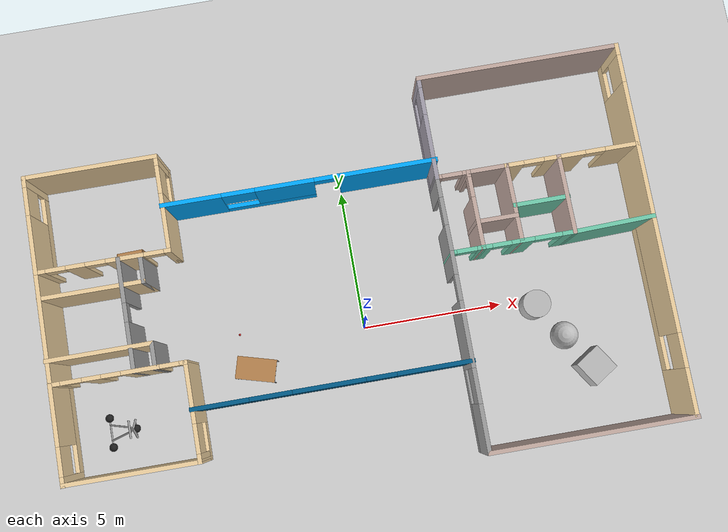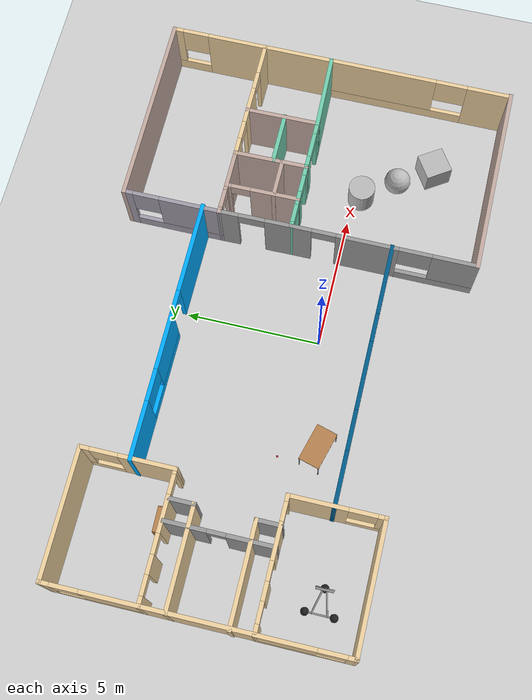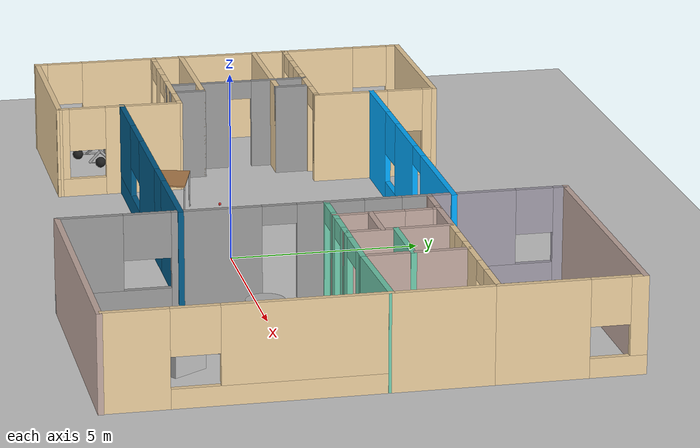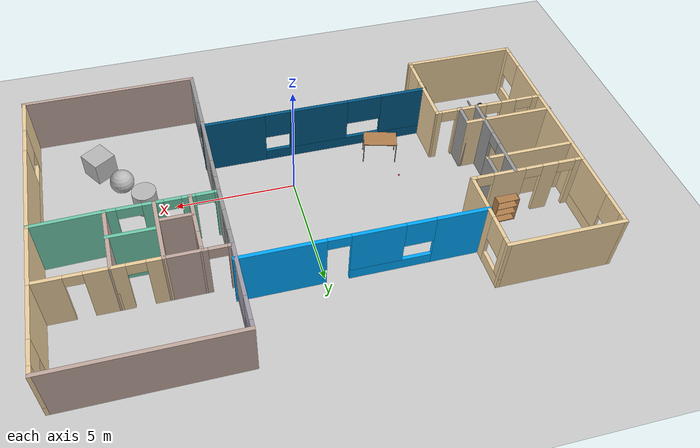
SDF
<sdf version="1.6">
 <world name="default">
  <light name="sun" type="directional">
   <pose>0 0 10 0 -0 0</pose>
   <diffuse>0.8 0.8 0.8 1</diffuse>
   <specular>0.1 0.1 0.1 1</specular>
   <attenuation>
    <range>1000</range>
    <constant>0.9</constant>
    <linear>0.01</linear>
    <quadratic>0.001</quadratic>
   </attenuation>
   <direction>-0.5 0.5 -1</direction>
  </light>
  <model name="ground_plane">
   <static>1</static>
   <link name="link">
    <collision name="collision">
     <geometry><plane><normal>0 0 1</normal><size>100 100</size></plane></geometry>
     <surface><friction><ode><mu>100</mu><mu2>50</mu2></ode></friction></surface>
    </collision>
    <visual name="visual">
     <cast_shadows>0</cast_shadows>
     <geometry><plane><normal>0 0 1</normal><size>100 100</size></plane></geometry>
     <material>
      <script><uri>file://media/materials/scripts/gazebo.material</uri><name>Gazebo/Grey</name></script>
     </material>
    </visual>
   </link>
  </model>
  <gravity>0 0 -9.8</gravity>
  <magnetic_field>6e-06 2.3e-05 -4.2e-05</magnetic_field>
  <atmosphere type="adiabatic"/>
  <physics name="default_physics" default="0" type="ode">
   <max_step_size>0.001</max_step_size>
   <real_time_factor>1</real_time_factor>
   <real_time_update_rate>1000</real_time_update_rate>
  </physics>
  <scene><ambient>0.4 0.4 0.4 1</ambient><background>0.7 0.7 0.7 1</background><shadows>1</shadows></scene>
  <spherical_coordinates>
   <surface_model>EARTH_WGS84</surface_model>
   <latitude_deg>0</latitude_deg>
   <longitude_deg>0</longitude_deg>
   <elevation>0</elevation>
   <heading_deg>0</heading_deg>
  </spherical_coordinates>
  <model name="building_1">
   <pose>-0.196 1.55734 0 0 -0 0</pose>
   <link name="Wall_0">
    <pose>10.6077 -3.05967 0 0 -0 1.5708</pose>
    <visual name="Wall_0_Visual_0">
     <pose>-2.67508 0 1.25 0 -0 0</pose>
     <geometry><box><size>1.64985 0.15 2.5</size></box></geometry>
     <material>
      <script><uri>file://media/materials/scripts/gazebo.material</uri><name>Gazebo/Grey</name></script>
      <ambient>0.921569 0.807843 0.615686 1</ambient>
     </material>
    </visual>
    <collision name="Wall_0_Collision_0">
     <geometry><box><size>1.64985 0.15 2.5</size></box></geometry>
     <pose>-2.67508 0 1.25 0 -0 0</pose>
    </collision>
    <visual name="Wall_0_Visual_1">
     <pose>0.824924 0 0.25 0 -0 0</pose>
     <geometry><box><size>5.35015 0.15 0.5</size></box></geometry>
     <material>
      <script><uri>file://media/materials/scripts/gazebo.material</uri><name>Gazebo/Grey</name></script>
      <ambient>0.921569 0.807843 0.615686 1</ambient>
     </material>
    </visual>
    <collision name="Wall_0_Collision_1">
     <geometry><box><size>5.35015 0.15 0.5</size></box></geometry>
     <pose>0.824924 0 0.25 0 -0 0</pose>
    </collision>
    <visual name="Wall_0_Visual_2">
     <pose>1.42468 0 1.5 0 -0 0</pose>
     <geometry><box><size>4.15065 0.15 2</size></box></geometry>
     <material>
      <script><uri>file://media/materials/scripts/gazebo.material</uri><name>Gazebo/Grey</name></script>
      <ambient>0.921569 0.807843 0.615686 1</ambient>
     </material>
    </visual>
    <collision name="Wall_0_Collision_2">
     <geometry><box><size>4.15065 0.15 2</size></box></geometry>
     <pose>1.42468 0 1.5 0 -0 0</pose>
    </collision>
    <visual name="Wall_0_Visual_3">
     <pose>-1.2504 0 1.9 0 -0 0</pose>
     <geometry><box><size>1.1995 0.15 1.2</size></box></geometry>
     <material>
      <script><uri>file://media/materials/scripts/gazebo.material</uri><name>Gazebo/Grey</name></script>
      <ambient>0.921569 0.807843 0.615686 1</ambient>
     </material>
    </visual>
    <collision name="Wall_0_Collision_3">
     <geometry><box><size>1.1995 0.15 1.2</size></box></geometry>
     <pose>-1.2504 0 1.9 0 -0 0</pose>
    </collision>
   </link>
   <link name="Wall_1">
    <collision name="Wall_1_Collision">
     <geometry><box><size>2.75 0.15 2.5</size></box></geometry>
     <pose>0 0 1.25 0 -0 0</pose>
    </collision>
    <visual name="Wall_1_Visual">
     <pose>0 0 1.25 0 -0 0</pose>
     <geometry><box><size>2.75 0.15 2.5</size></box></geometry>
     <material>
      <script><uri>file://media/materials/scripts/gazebo.material</uri><name>Gazebo/Grey</name></script>
      <ambient>0.921569 0.807843 0.615686 1</ambient>
     </material>
    </visual>
    <pose>10.6077 1.66533 0 0 -0 1.5708</pose>
   </link>
   <link name="Wall_11">
    <pose>3.50766 4.76533 0 0 0 -1.5708</pose>
    <visual name="Wall_11_Visual_0">
     <pose>-1.66535 0 1.25 0 -0 0</pose>
     <geometry><box><size>0.419296 0.15 2.5</size></box></geometry>
     <material>
      <script><uri>file://media/materials/scripts/gazebo.material</uri><name>Gazebo/Grey</name></script>
      <ambient>0.627451 0.607843 0.658824 1</ambient>
     </material>
    </visual>
    <collision name="Wall_11_Collision_0">
     <geometry><box><size>0.419296 0.15 2.5</size></box></geometry>
     <pose>-1.66535 0 1.25 0 -0 0</pose>
    </collision>
    <visual name="Wall_11_Visual_1">
     <pose>0.209648 0 0.25 0 -0 0</pose>
     <geometry><box><size>3.3307 0.15 0.5</size></box></geometry>
     <material>
      <script><uri>file://media/materials/scripts/gazebo.material</uri><name>Gazebo/Grey</name></script>
      <ambient>0.627451 0.607843 0.658824 1</ambient>
     </material>
    </visual>
    <collision name="Wall_11_Collision_1">
     <geometry><box><size>3.3307 0.15 0.5</size></box></geometry>
     <pose>0.209648 0 0.25 0 -0 0</pose>
    </collision>
    <visual name="Wall_11_Visual_2">
     <pose>0.700272 0 1.5 0 -0 0</pose>
     <geometry><box><size>2.34945 0.15 2</size></box></geometry>
     <material>
      <script><uri>file://media/materials/scripts/gazebo.material</uri><name>Gazebo/Grey</name></script>
      <ambient>0.627451 0.607843 0.658824 1</ambient>
     </material>
    </visual>
    <collision name="Wall_11_Collision_2">
     <geometry><box><size>2.34945 0.15 2</size></box></geometry>
     <pose>0.700272 0 1.5 0 -0 0</pose>
    </collision>
    <visual name="Wall_11_Visual_3">
     <pose>-0.96508 0 1.9 0 -0 0</pose>
     <geometry><box><size>0.981249 0.15 1.2</size></box></geometry>
     <material>
      <script><uri>file://media/materials/scripts/gazebo.material</uri><name>Gazebo/Grey</name></script>
      <ambient>0.627451 0.607843 0.658824 1</ambient>
     </material>
    </visual>
    <collision name="Wall_11_Collision_3">
     <geometry><box><size>0.981249 0.15 1.2</size></box></geometry>
     <pose>-0.96508 0 1.9 0 -0 0</pose>
    </collision>
   </link>
   <link name="Wall_15">
    <pose>4.05766 2.96533 0 0 -0 0</pose>
    <visual name="Wall_15_Visual_0">
     <pose>-0.500149 0 1.25 0 -0 0</pose>
     <geometry><box><size>0.249701 0.15 2.5</size></box></geometry>
     <material>
      <script><uri>file://media/materials/scripts/gazebo.material</uri><name>Gazebo/Grey</name></script>
      <ambient>0.760784 0.662745 0.627451 1</ambient>
     </material>
    </visual>
    <collision name="Wall_15_Collision_0">
     <geometry><box><size>0.249701 0.15 2.5</size></box></geometry>
     <pose>-0.500149 0 1.25 0 -0 0</pose>
    </collision>
    <visual name="Wall_15_Visual_1">
     <pose>0.482342 0 1.25 0 -0 0</pose>
     <geometry><box><size>0.285316 0.15 2.5</size></box></geometry>
     <material>
      <script><uri>file://media/materials/scripts/gazebo.material</uri><name>Gazebo/Grey</name></script>
      <ambient>0.760784 0.662745 0.627451 1</ambient>
     </material>
    </visual>
    <collision name="Wall_15_Collision_1">
     <geometry><box><size>0.285316 0.15 2.5</size></box></geometry>
     <pose>0.482342 0 1.25 0 -0 0</pose>
    </collision>
    <visual name="Wall_15_Visual_2">
     <pose>-0.017807 0 2.25 0 -0 0</pose>
     <geometry><box><size>0.714982 0.15 0.5</size></box></geometry>
     <material>
      <script><uri>file://media/materials/scripts/gazebo.material</uri><name>Gazebo/Grey</name></script>
      <ambient>0.760784 0.662745 0.627451 1</ambient>
     </material>
    </visual>
    <collision name="Wall_15_Collision_2">
     <geometry><box><size>0.714982 0.15 0.5</size></box></geometry>
     <pose>-0.017807 0 2.25 0 -0 0</pose>
    </collision>
   </link>
   <link name="Wall_16">
    <collision name="Wall_16_Collision">
     <geometry><box><size>1.5 0.15 2.5</size></box></geometry>
     <pose>0 0 1.25 0 -0 0</pose>
    </collision>
    <visual name="Wall_16_Visual">
     <pose>0 0 1.25 0 -0 0</pose>
     <geometry><box><size>1.5 0.15 2.5</size></box></geometry>
     <material>
      <script><uri>file://media/materials/scripts/gazebo.material</uri><name>Gazebo/Grey</name></script>
      <ambient>0.760784 0.662745 0.627451 1</ambient>
     </material>
    </visual>
    <pose>5.28266 2.96533 0 0 -0 0</pose>
   </link>
   <link name="Wall_17">
    <pose>6.88266 2.96533 0 0 -0 0</pose>
    <visual name="Wall_17_Visual_0">
     <pose>-0.653322 0 1.25 0 -0 0</pose>
     <geometry><box><size>0.693356 0.15 2.5</size></box></geometry>
     <material>
      <script><uri>file://media/materials/scripts/gazebo.material</uri><name>Gazebo/Grey</name></script>
      <ambient>0.921569 0.807843 0.615686 1</ambient>
     </material>
    </visual>
    <collision name="Wall_17_Collision_0">
     <geometry><box><size>0.693356 0.15 2.5</size></box></geometry>
     <pose>-0.653322 0 1.25 0 -0 0</pose>
    </collision>
    <visual name="Wall_17_Visual_1">
     <pose>0.704169 0 1.25 0 -0 0</pose>
     <geometry><box><size>0.591662 0.15 2.5</size></box></geometry>
     <material>
      <script><uri>file://media/materials/scripts/gazebo.material</uri><name>Gazebo/Grey</name></script>
      <ambient>0.921569 0.807843 0.615686 1</ambient>
     </material>
    </visual>
    <collision name="Wall_17_Collision_1">
     <geometry><box><size>0.591662 0.15 2.5</size></box></geometry>
     <pose>0.704169 0 1.25 0 -0 0</pose>
    </collision>
    <visual name="Wall_17_Visual_2">
     <pose>0.050847 0 2.25 0 -0 0</pose>
     <geometry><box><size>0.714982 0.15 0.5</size></box></geometry>
     <material>
      <script><uri>file://media/materials/scripts/gazebo.material</uri><name>Gazebo/Grey</name></script>
      <ambient>0.921569 0.807843 0.615686 1</ambient>
     </material>
    </visual>
    <collision name="Wall_17_Collision_2">
     <geometry><box><size>0.714982 0.15 0.5</size></box></geometry>
     <pose>0.050847 0 2.25 0 -0 0</pose>
    </collision>
   </link>
   <link name="Wall_18">
    <pose>9.20766 2.96533 0 0 -0 0</pose>
    <visual name="Wall_18_Visual_0">
     <pose>-0.963773 0 1.25 0 -0 0</pose>
     <geometry><box><size>1.02245 0.15 2.5</size></box></geometry>
     <material>
      <script><uri>file://media/materials/scripts/gazebo.material</uri><name>Gazebo/Grey</name></script>
      <ambient>0.921569 0.807843 0.615686 1</ambient>
     </material>
    </visual>
    <collision name="Wall_18_Collision_0">
     <geometry><box><size>1.02245 0.15 2.5</size></box></geometry>
     <pose>-0.963773 0 1.25 0 -0 0</pose>
    </collision>
    <visual name="Wall_18_Visual_1">
     <pose>0.85844 0 1.25 0 -0 0</pose>
     <geometry><box><size>1.23312 0.15 2.5</size></box></geometry>
     <material>
      <script><uri>file://media/materials/scripts/gazebo.material</uri><name>Gazebo/Grey</name></script>
      <ambient>0.921569 0.807843 0.615686 1</ambient>
     </material>
    </visual>
    <collision name="Wall_18_Collision_1">
     <geometry><box><size>1.23312 0.15 2.5</size></box></geometry>
     <pose>0.85844 0 1.25 0 -0 0</pose>
    </collision>
    <visual name="Wall_18_Visual_2">
     <pose>-0.105333 0 2.25 0 -0 0</pose>
     <geometry><box><size>0.694425 0.15 0.5</size></box></geometry>
     <material>
      <script><uri>file://media/materials/scripts/gazebo.material</uri><name>Gazebo/Grey</name></script>
      <ambient>0.921569 0.807843 0.615686 1</ambient>
     </material>
    </visual>
    <collision name="Wall_18_Collision_2">
     <geometry><box><size>0.694425 0.15 0.5</size></box></geometry>
     <pose>-0.105333 0 2.25 0 -0 0</pose>
    </collision>
   </link>
   <link name="Wall_2">
    <pose>10.6077 4.76533 0 0 -0 1.5708</pose>
    <visual name="Wall_2_Visual_0">
     <pose>-0.712356 0 1.25 0 -0 0</pose>
     <geometry><box><size>2.32529 0.15 2.5</size></box></geometry>
     <material>
      <script><uri>file://media/materials/scripts/gazebo.material</uri><name>Gazebo/Grey</name></script>
      <ambient>0.921569 0.807843 0.615686 1</ambient>
     </material>
    </visual>
    <collision name="Wall_2_Collision_0">
     <geometry><box><size>2.32529 0.15 2.5</size></box></geometry>
     <pose>-0.712356 0 1.25 0 -0 0</pose>
    </collision>
    <visual name="Wall_2_Visual_1">
     <pose>1.16264 0 0.25 0 -0 0</pose>
     <geometry><box><size>1.42471 0.15 0.5</size></box></geometry>
     <material>
      <script><uri>file://media/materials/scripts/gazebo.material</uri><name>Gazebo/Grey</name></script>
      <ambient>0.921569 0.807843 0.615686 1</ambient>
     </material>
    </visual>
    <collision name="Wall_2_Collision_1">
     <geometry><box><size>1.42471 0.15 0.5</size></box></geometry>
     <pose>1.16264 0 0.25 0 -0 0</pose>
    </collision>
    <visual name="Wall_2_Visual_2">
     <pose>1.65931 0 1.5 0 -0 0</pose>
     <geometry><box><size>0.431379 0.15 2</size></box></geometry>
     <material>
      <script><uri>file://media/materials/scripts/gazebo.material</uri><name>Gazebo/Grey</name></script>
      <ambient>0.921569 0.807843 0.615686 1</ambient>
     </material>
    </visual>
    <collision name="Wall_2_Collision_2">
     <geometry><box><size>0.431379 0.15 2</size></box></geometry>
     <pose>1.65931 0 1.5 0 -0 0</pose>
    </collision>
    <visual name="Wall_2_Visual_3">
     <pose>0.946955 0 1.9 0 -0 0</pose>
     <geometry><box><size>0.993332 0.15 1.2</size></box></geometry>
     <material>
      <script><uri>file://media/materials/scripts/gazebo.material</uri><name>Gazebo/Grey</name></script>
      <ambient>0.921569 0.807843 0.615686 1</ambient>
     </material>
    </visual>
    <collision name="Wall_2_Collision_3">
     <geometry><box><size>0.993332 0.15 1.2</size></box></geometry>
     <pose>0.946955 0 1.9 0 -0 0</pose>
    </collision>
   </link>
   <link name="Wall_20">
    <pose>4.08783 0.284672 0 0 -0 0</pose>
    <visual name="Wall_20_Visual_0">
     <pose>-0.502297 0 1.25 0 -0 0</pose>
     <geometry><box><size>0.245405 0.15 2.5</size></box></geometry>
     <material>
      <script><uri>file://media/materials/scripts/gazebo.material</uri><name>Gazebo/Grey</name></script>
      <ambient>0.435294 0.796078 0.67451 1</ambient>
     </material>
    </visual>
    <collision name="Wall_20_Collision_0">
     <geometry><box><size>0.245405 0.15 2.5</size></box></geometry>
     <pose>-0.502297 0 1.25 0 -0 0</pose>
    </collision>
    <visual name="Wall_20_Visual_1">
     <pose>0.480194 0 1.25 0 -0 0</pose>
     <geometry><box><size>0.289613 0.15 2.5</size></box></geometry>
     <material>
      <script><uri>file://media/materials/scripts/gazebo.material</uri><name>Gazebo/Grey</name></script>
      <ambient>0.435294 0.796078 0.67451 1</ambient>
     </material>
    </visual>
    <collision name="Wall_20_Collision_1">
     <geometry><box><size>0.289613 0.15 2.5</size></box></geometry>
     <pose>0.480194 0 1.25 0 -0 0</pose>
    </collision>
    <visual name="Wall_20_Visual_2">
     <pose>-0.022104 0 2.25 0 -0 0</pose>
     <geometry><box><size>0.714982 0.15 0.5</size></box></geometry>
     <material>
      <script><uri>file://media/materials/scripts/gazebo.material</uri><name>Gazebo/Grey</name></script>
      <ambient>0.435294 0.796078 0.67451 1</ambient>
     </material>
    </visual>
    <collision name="Wall_20_Collision_2">
     <geometry><box><size>0.714982 0.15 0.5</size></box></geometry>
     <pose>-0.022104 0 2.25 0 -0 0</pose>
    </collision>
   </link>
   <link name="Wall_21">
    <pose>5.31283 0.284672 0 0 -0 0</pose>
    <visual name="Wall_21_Visual_0">
     <pose>-0.555432 0 1.25 0 -0 0</pose>
     <geometry><box><size>0.389136 0.15 2.5</size></box></geometry>
     <material>
      <script><uri>file://media/materials/scripts/gazebo.material</uri><name>Gazebo/Grey</name></script>
      <ambient>0.435294 0.796078 0.67451 1</ambient>
     </material>
    </visual>
    <collision name="Wall_21_Collision_0">
     <geometry><box><size>0.389136 0.15 2.5</size></box></geometry>
     <pose>-0.555432 0 1.25 0 -0 0</pose>
    </collision>
    <visual name="Wall_21_Visual_1">
     <pose>0.531502 0 1.25 0 -0 0</pose>
     <geometry><box><size>0.436997 0.15 2.5</size></box></geometry>
     <material>
      <script><uri>file://media/materials/scripts/gazebo.material</uri><name>Gazebo/Grey</name></script>
      <ambient>0.435294 0.796078 0.67451 1</ambient>
     </material>
    </visual>
    <collision name="Wall_21_Collision_1">
     <geometry><box><size>0.436997 0.15 2.5</size></box></geometry>
     <pose>0.531502 0 1.25 0 -0 0</pose>
    </collision>
    <visual name="Wall_21_Visual_2">
     <pose>-0.023931 0 2.25 0 -0 0</pose>
     <geometry><box><size>0.673867 0.15 0.5</size></box></geometry>
     <material>
      <script><uri>file://media/materials/scripts/gazebo.material</uri><name>Gazebo/Grey</name></script>
      <ambient>0.435294 0.796078 0.67451 1</ambient>
     </material>
    </visual>
    <collision name="Wall_21_Collision_2">
     <geometry><box><size>0.673867 0.15 0.5</size></box></geometry>
     <pose>-0.023931 0 2.25 0 -0 0</pose>
    </collision>
   </link>
   <link name="Wall_22">
    <pose>6.91283 0.284672 0 0 -0 0</pose>
    <visual name="Wall_22_Visual_0">
     <pose>-0.740361 0 1.25 0 -0 0</pose>
     <geometry><box><size>0.519278 0.15 2.5</size></box></geometry>
     <material>
      <script><uri>file://media/materials/scripts/gazebo.material</uri><name>Gazebo/Grey</name></script>
      <ambient>0.435294 0.796078 0.67451 1</ambient>
     </material>
    </visual>
    <collision name="Wall_22_Collision_0">
     <geometry><box><size>0.519278 0.15 2.5</size></box></geometry>
     <pose>-0.740361 0 1.25 0 -0 0</pose>
    </collision>
    <visual name="Wall_22_Visual_1">
     <pose>0.740475 0 1.25 0 -0 0</pose>
     <geometry><box><size>0.519049 0.15 2.5</size></box></geometry>
     <material>
      <script><uri>file://media/materials/scripts/gazebo.material</uri><name>Gazebo/Grey</name></script>
      <ambient>0.435294 0.796078 0.67451 1</ambient>
     </material>
    </visual>
    <collision name="Wall_22_Collision_1">
     <geometry><box><size>0.519049 0.15 2.5</size></box></geometry>
     <pose>0.740475 0 1.25 0 -0 0</pose>
    </collision>
    <visual name="Wall_22_Visual_2">
     <pose>0.000114 0 2.25 0 -0 0</pose>
     <geometry><box><size>0.961673 0.15 0.5</size></box></geometry>
     <material>
      <script><uri>file://media/materials/scripts/gazebo.material</uri><name>Gazebo/Grey</name></script>
      <ambient>0.435294 0.796078 0.67451 1</ambient>
     </material>
    </visual>
    <collision name="Wall_22_Collision_2">
     <geometry><box><size>0.961673 0.15 0.5</size></box></geometry>
     <pose>0.000114 0 2.25 0 -0 0</pose>
    </collision>
   </link>
   <link name="Wall_25">
    <pose>4.62274 1.625 0 0 0 -1.55954</pose>
    <visual name="Wall_25_Visual_0">
     <pose>-1.29279 0 1.25 0 -0 0</pose>
     <geometry><box><size>0.245238 0.15 2.5</size></box></geometry>
     <material>
      <script><uri>file://media/materials/scripts/gazebo.material</uri><name>Gazebo/Grey</name></script>
      <ambient>0.760784 0.662745 0.627451 1</ambient>
     </material>
    </visual>
    <collision name="Wall_25_Collision_0">
     <geometry><box><size>0.245238 0.15 2.5</size></box></geometry>
     <pose>-1.29279 0 1.25 0 -0 0</pose>
    </collision>
    <visual name="Wall_25_Visual_1">
     <pose>0.482068 0 1.25 0 -0 0</pose>
     <geometry><box><size>1.86669 0.15 2.5</size></box></geometry>
     <material>
      <script><uri>file://media/materials/scripts/gazebo.material</uri><name>Gazebo/Grey</name></script>
      <ambient>0.760784 0.662745 0.627451 1</ambient>
     </material>
    </visual>
    <collision name="Wall_25_Collision_1">
     <geometry><box><size>1.86669 0.15 2.5</size></box></geometry>
     <pose>0.482068 0 1.25 0 -0 0</pose>
    </collision>
    <visual name="Wall_25_Visual_2">
     <pose>-0.810726 0 2.25 0 -0 0</pose>
     <geometry><box><size>0.718899 0.15 0.5</size></box></geometry>
     <material>
      <script><uri>file://media/materials/scripts/gazebo.material</uri><name>Gazebo/Grey</name></script>
      <ambient>0.760784 0.662745 0.627451 1</ambient>
     </material>
    </visual>
    <collision name="Wall_25_Collision_2">
     <geometry><box><size>0.718899 0.15 0.5</size></box></geometry>
     <pose>-0.810726 0 2.25 0 -0 0</pose>
    </collision>
   </link>
   <link name="Wall_27">
    <collision name="Wall_27_Collision">
     <geometry><box><size>2.83083 0.15 2.5</size></box></geometry>
     <pose>0 0 1.25 0 -0 0</pose>
    </collision>
    <visual name="Wall_27_Visual">
     <pose>0 0 1.25 0 -0 0</pose>
     <geometry><box><size>2.83083 0.15 2.5</size></box></geometry>
     <material>
      <script><uri>file://media/materials/scripts/gazebo.material</uri><name>Gazebo/Grey</name></script>
      <ambient>0.760784 0.662745 0.627451 1</ambient>
     </material>
    </visual>
    <pose>5.97274 1.625 0 0 0 -1.55954</pose>
   </link>
   <link name="Wall_29">
    <collision name="Wall_29_Collision">
     <geometry><box><size>2.83083 0.15 2.5</size></box></geometry>
     <pose>0 0 1.25 0 -0 0</pose>
    </collision>
    <visual name="Wall_29_Visual">
     <pose>0 0 1.25 0 -0 0</pose>
     <geometry><box><size>2.83083 0.15 2.5</size></box></geometry>
     <material>
      <script><uri>file://media/materials/scripts/gazebo.material</uri><name>Gazebo/Grey</name></script>
      <ambient>0.760784 0.662745 0.627451 1</ambient>
     </material>
    </visual>
    <pose>7.82274 1.625 0 0 0 -1.55954</pose>
   </link>
   <link name="Wall_31">
    <collision name="Wall_31_Collision">
     <geometry><box><size>1.5 0.15 2.5</size></box></geometry>
     <pose>0 0 1.25 0 -0 0</pose>
    </collision>
    <visual name="Wall_31_Visual">
     <pose>0 0 1.25 0 -0 0</pose>
     <geometry><box><size>1.5 0.15 2.5</size></box></geometry>
     <material>
      <script><uri>file://media/materials/scripts/gazebo.material</uri><name>Gazebo/Grey</name></script>
      <ambient>0.760784 0.662745 0.627451 1</ambient>
     </material>
    </visual>
    <pose>5.29549 1.19333 0 0 -0 0</pose>
   </link>
   <link name="Wall_33">
    <collision name="Wall_33_Collision">
     <geometry><box><size>2 0.15 2.5</size></box></geometry>
     <pose>0 0 1.25 0 -0 0</pose>
    </collision>
    <visual name="Wall_33_Visual">
     <pose>0 0 1.25 0 -0 0</pose>
     <geometry><box><size>2 0.15 2.5</size></box></geometry>
     <material>
      <script><uri>file://media/materials/scripts/gazebo.material</uri><name>Gazebo/Grey</name></script>
      <ambient>0.435294 0.796078 0.67451 1</ambient>
     </material>
    </visual>
    <pose>6.91815 1.54133 0 0 -0 0</pose>
   </link>
   <link name="Wall_35">
    <pose>3.52274 1.625 0 0 0 -1.55954</pose>
    <visual name="Wall_35_Visual_0">
     <pose>-1.02107 0 1.25 0 -0 0</pose>
     <geometry><box><size>0.78869 0.15 2.5</size></box></geometry>
     <material>
      <script><uri>file://media/materials/scripts/gazebo.material</uri><name>Gazebo/Grey</name></script>
      <ambient>0.635294 0.619608 0.658824 1</ambient>
     </material>
    </visual>
    <collision name="Wall_35_Collision_0">
     <geometry><box><size>0.78869 0.15 2.5</size></box></geometry>
     <pose>-1.02107 0 1.25 0 -0 0</pose>
    </collision>
    <visual name="Wall_35_Visual_1">
     <pose>0.885093 0 1.25 0 -0 0</pose>
     <geometry><box><size>1.06064 0.15 2.5</size></box></geometry>
     <material>
      <script><uri>file://media/materials/scripts/gazebo.material</uri><name>Gazebo/Grey</name></script>
      <ambient>0.635294 0.619608 0.658824 1</ambient>
     </material>
    </visual>
    <collision name="Wall_35_Collision_1">
     <geometry><box><size>1.06064 0.15 2.5</size></box></geometry>
     <pose>0.885093 0 1.25 0 -0 0</pose>
    </collision>
    <visual name="Wall_35_Visual_2">
     <pose>-0.135975 0 2.25 0 -0 0</pose>
     <geometry><box><size>0.981496 0.15 0.5</size></box></geometry>
     <material>
      <script><uri>file://media/materials/scripts/gazebo.material</uri><name>Gazebo/Grey</name></script>
      <ambient>0.635294 0.619608 0.658824 1</ambient>
     </material>
    </visual>
    <collision name="Wall_35_Collision_2">
     <geometry><box><size>0.981496 0.15 0.5</size></box></geometry>
     <pose>-0.135975 0 2.25 0 -0 0</pose>
    </collision>
   </link>
   <link name="Wall_37">
    <pose>-1.22369 3.60062 0 0 -0 0</pose>
    <visual name="Wall_37_Visual_0">
     <pose>-3.80255 0 1.25 0 -0 0</pose>
     <geometry><box><size>2.14491 0.15 2.5</size></box></geometry>
     <material>
      <script><uri>file://media/materials/scripts/gazebo.material</uri><name>Gazebo/Grey</name></script>
      <ambient>0 0.666667 1 1</ambient>
     </material>
    </visual>
    <collision name="Wall_37_Collision_0">
     <geometry><box><size>2.14491 0.15 2.5</size></box></geometry>
     <pose>-3.80255 0 1.25 0 -0 0</pose>
    </collision>
    <visual name="Wall_37_Visual_1">
     <pose>3.14793 0 1.25 0 -0 0</pose>
     <geometry><box><size>3.45414 0.15 2.5</size></box></geometry>
     <material>
      <script><uri>file://media/materials/scripts/gazebo.material</uri><name>Gazebo/Grey</name></script>
      <ambient>0 0.666667 1 1</ambient>
     </material>
    </visual>
    <collision name="Wall_37_Collision_1">
     <geometry><box><size>3.45414 0.15 2.5</size></box></geometry>
     <pose>3.14793 0 1.25 0 -0 0</pose>
    </collision>
    <visual name="Wall_37_Visual_2">
     <pose>-1.10462 0 0.25 0 -0 0</pose>
     <geometry><box><size>3.25095 0.15 0.5</size></box></geometry>
     <material>
      <script><uri>file://media/materials/scripts/gazebo.material</uri><name>Gazebo/Grey</name></script>
      <ambient>0 0.666667 1 1</ambient>
     </material>
    </visual>
    <collision name="Wall_37_Collision_2">
     <geometry><box><size>3.25095 0.15 0.5</size></box></geometry>
     <pose>-1.10462 0 0.25 0 -0 0</pose>
    </collision>
    <visual name="Wall_37_Visual_3">
     <pose>-0.519342 0 1.5 0 -0 0</pose>
     <geometry><box><size>2.0804 0.15 2</size></box></geometry>
     <material>
      <script><uri>file://media/materials/scripts/gazebo.material</uri><name>Gazebo/Grey</name></script>
      <ambient>0 0.666667 1 1</ambient>
     </material>
    </visual>
    <collision name="Wall_37_Collision_3">
     <geometry><box><size>2.0804 0.15 2</size></box></geometry>
     <pose>-0.519342 0 1.5 0 -0 0</pose>
    </collision>
    <visual name="Wall_37_Visual_4">
     <pose>-2.14482 0 1.9 0 -0 0</pose>
     <geometry><box><size>1.17055 0.15 1.2</size></box></geometry>
     <material>
      <script><uri>file://media/materials/scripts/gazebo.material</uri><name>Gazebo/Grey</name></script>
      <ambient>0 0.666667 1 1</ambient>
     </material>
    </visual>
    <collision name="Wall_37_Collision_4">
     <geometry><box><size>1.17055 0.15 1.2</size></box></geometry>
     <pose>-2.14482 0 1.9 0 -0 0</pose>
    </collision>
    <visual name="Wall_37_Visual_5">
     <pose>0.970856 0 2.25 0 -0 0</pose>
     <geometry><box><size>0.9 0.15 0.5</size></box></geometry>
     <material>
      <script><uri>file://media/materials/scripts/gazebo.material</uri><name>Gazebo/Grey</name></script>
      <ambient>0 0.666667 1 1</ambient>
     </material>
    </visual>
    <collision name="Wall_37_Collision_5">
     <geometry><box><size>0.9 0.15 0.5</size></box></geometry>
     <pose>0.970856 0 2.25 0 -0 0</pose>
    </collision>
   </link>
   <link name="Wall_39">
    <pose>-5.99933 3.69534 0 0 -0 1.5708</pose>
    <visual name="Wall_39_Visual_0">
     <pose>-0.7017 0 1.25 0 -0 0</pose>
     <geometry><box><size>2.0966 0.15 2.5</size></box></geometry>
     <material>
      <script><uri>file://media/materials/scripts/gazebo.material</uri><name>Gazebo/Grey</name></script>
      <ambient>0.921569 0.807843 0.615686 1</ambient>
     </material>
    </visual>
    <collision name="Wall_39_Collision_0">
     <geometry><box><size>2.0966 0.15 2.5</size></box></geometry>
     <pose>-0.7017 0 1.25 0 -0 0</pose>
    </collision>
    <visual name="Wall_39_Visual_1">
     <pose>1.0483 0 0.25 0 -0 0</pose>
     <geometry><box><size>1.4034 0.15 0.5</size></box></geometry>
     <material>
      <script><uri>file://media/materials/scripts/gazebo.material</uri><name>Gazebo/Grey</name></script>
      <ambient>0.921569 0.807843 0.615686 1</ambient>
     </material>
    </visual>
    <collision name="Wall_39_Collision_1">
     <geometry><box><size>1.4034 0.15 0.5</size></box></geometry>
     <pose>1.0483 0 0.25 0 -0 0</pose>
    </collision>
    <visual name="Wall_39_Visual_2">
     <pose>1.54557 0 1.5 0 -0 0</pose>
     <geometry><box><size>0.40886 0.15 2</size></box></geometry>
     <material>
      <script><uri>file://media/materials/scripts/gazebo.material</uri><name>Gazebo/Grey</name></script>
      <ambient>0.921569 0.807843 0.615686 1</ambient>
     </material>
    </visual>
    <collision name="Wall_39_Collision_2">
     <geometry><box><size>0.40886 0.15 2</size></box></geometry>
     <pose>1.54557 0 1.5 0 -0 0</pose>
    </collision>
    <visual name="Wall_39_Visual_3">
     <pose>0.84387 0 1.9 0 -0 0</pose>
     <geometry><box><size>0.994541 0.15 1.2</size></box></geometry>
     <material>
      <script><uri>file://media/materials/scripts/gazebo.material</uri><name>Gazebo/Grey</name></script>
      <ambient>0.921569 0.807843 0.615686 1</ambient>
     </material>
    </visual>
    <collision name="Wall_39_Collision_3">
     <geometry><box><size>0.994541 0.15 1.2</size></box></geometry>
     <pose>0.84387 0 1.9 0 -0 0</pose>
    </collision>
   </link>
   <link name="Wall_40">
    <collision name="Wall_40_Collision">
     <geometry><box><size>4.75 0.15 2.5</size></box></geometry>
     <pose>0 0 1.25 0 -0 0</pose>
    </collision>
    <visual name="Wall_40_Visual">
     <pose>0 0 1.25 0 -0 0</pose>
     <geometry><box><size>4.75 0.15 2.5</size></box></geometry>
     <material>
      <script><uri>file://media/materials/scripts/gazebo.material</uri><name>Gazebo/Grey</name></script>
      <ambient>0.921569 0.807843 0.615686 1</ambient>
     </material>
    </visual>
    <pose>-8.29933 5.37033 0 0 -0 3.14159</pose>
   </link>
   <link name="Wall_41">
    <pose>-10.5993 3.69534 0 0 0 -1.5708</pose>
    <visual name="Wall_41_Visual_0">
     <pose>-1.54557 0 1.25 0 -0 0</pose>
     <geometry><box><size>0.40886 0.15 2.5</size></box></geometry>
     <material>
      <script><uri>file://media/materials/scripts/gazebo.material</uri><name>Gazebo/Grey</name></script>
      <ambient>0.921569 0.807843 0.615686 1</ambient>
     </material>
    </visual>
    <collision name="Wall_41_Collision_0">
     <geometry><box><size>0.40886 0.15 2.5</size></box></geometry>
     <pose>-1.54557 0 1.25 0 -0 0</pose>
    </collision>
    <visual name="Wall_41_Visual_1">
     <pose>0.20443 0 0.25 0 -0 0</pose>
     <geometry><box><size>3.09114 0.15 0.5</size></box></geometry>
     <material>
      <script><uri>file://media/materials/scripts/gazebo.material</uri><name>Gazebo/Grey</name></script>
      <ambient>0.921569 0.807843 0.615686 1</ambient>
     </material>
    </visual>
    <collision name="Wall_41_Collision_1">
     <geometry><box><size>3.09114 0.15 0.5</size></box></geometry>
     <pose>0.20443 0 0.25 0 -0 0</pose>
    </collision>
    <visual name="Wall_41_Visual_2">
     <pose>0.7017 0 1.5 0 -0 0</pose>
     <geometry><box><size>2.0966 0.15 2</size></box></geometry>
     <material>
      <script><uri>file://media/materials/scripts/gazebo.material</uri><name>Gazebo/Grey</name></script>
      <ambient>0.921569 0.807843 0.615686 1</ambient>
     </material>
    </visual>
    <collision name="Wall_41_Collision_2">
     <geometry><box><size>2.0966 0.15 2</size></box></geometry>
     <pose>0.7017 0 1.5 0 -0 0</pose>
    </collision>
    <visual name="Wall_41_Visual_3">
     <pose>-0.84387 0 1.9 0 -0 0</pose>
     <geometry><box><size>0.994541 0.15 1.2</size></box></geometry>
     <material>
      <script><uri>file://media/materials/scripts/gazebo.material</uri><name>Gazebo/Grey</name></script>
      <ambient>0.921569 0.807843 0.615686 1</ambient>
     </material>
    </visual>
    <collision name="Wall_41_Collision_3">
     <geometry><box><size>0.994541 0.15 1.2</size></box></geometry>
     <pose>-0.84387 0 1.9 0 -0 0</pose>
    </collision>
   </link>
   <link name="Wall_42">
    <pose>-8.29933 2.02034 0 0 -0 0</pose>
    <visual name="Wall_42_Visual_0">
     <pose>-2.17331 0 1.25 0 -0 0</pose>
     <geometry><box><size>0.403378 0.15 2.5</size></box></geometry>
     <material>
      <script><uri>file://media/materials/scripts/gazebo.material</uri><name>Gazebo/Grey</name></script>
      <ambient>0.921569 0.807843 0.615686 1</ambient>
     </material>
    </visual>
    <collision name="Wall_42_Collision_0">
     <geometry><box><size>0.403378 0.15 2.5</size></box></geometry>
     <pose>-2.17331 0 1.25 0 -0 0</pose>
    </collision>
    <visual name="Wall_42_Visual_1">
     <pose>-0.940648 0 1.25 0 -0 0</pose>
     <geometry><box><size>0.66714 0.15 2.5</size></box></geometry>
     <material>
      <script><uri>file://media/materials/scripts/gazebo.material</uri><name>Gazebo/Grey</name></script>
      <ambient>0.921569 0.807843 0.615686 1</ambient>
     </material>
    </visual>
    <collision name="Wall_42_Collision_1">
     <geometry><box><size>0.66714 0.15 2.5</size></box></geometry>
     <pose>-0.940648 0 1.25 0 -0 0</pose>
    </collision>
    <visual name="Wall_42_Visual_2">
     <pose>0.760562 0 1.25 0 -0 0</pose>
     <geometry><box><size>1.31664 0.15 2.5</size></box></geometry>
     <material>
      <script><uri>file://media/materials/scripts/gazebo.material</uri><name>Gazebo/Grey</name></script>
      <ambient>0.921569 0.807843 0.615686 1</ambient>
     </material>
    </visual>
    <collision name="Wall_42_Collision_2">
     <geometry><box><size>1.31664 0.15 2.5</size></box></geometry>
     <pose>0.760562 0 1.25 0 -0 0</pose>
    </collision>
    <visual name="Wall_42_Visual_3">
     <pose>2.24564 0 1.25 0 -0 0</pose>
     <geometry><box><size>0.258715 0.15 2.5</size></box></geometry>
     <material>
      <script><uri>file://media/materials/scripts/gazebo.material</uri><name>Gazebo/Grey</name></script>
      <ambient>0.921569 0.807843 0.615686 1</ambient>
     </material>
    </visual>
    <collision name="Wall_42_Collision_3">
     <geometry><box><size>0.258715 0.15 2.5</size></box></geometry>
     <pose>2.24564 0 1.25 0 -0 0</pose>
    </collision>
    <visual name="Wall_42_Visual_4">
     <pose>-1.62292 0 2.25 0 -0 0</pose>
     <geometry><box><size>0.697404 0.15 0.5</size></box></geometry>
     <material>
      <script><uri>file://media/materials/scripts/gazebo.material</uri><name>Gazebo/Grey</name></script>
      <ambient>0.921569 0.807843 0.615686 1</ambient>
     </material>
    </visual>
    <collision name="Wall_42_Collision_4">
     <geometry><box><size>0.697404 0.15 0.5</size></box></geometry>
     <pose>-1.62292 0 2.25 0 -0 0</pose>
    </collision>
    <visual name="Wall_42_Visual_5">
     <pose>-0.252418 0 2.25 0 -0 0</pose>
     <geometry><box><size>0.709321 0.15 0.5</size></box></geometry>
     <material>
      <script><uri>file://media/materials/scripts/gazebo.material</uri><name>Gazebo/Grey</name></script>
      <ambient>0.921569 0.807843 0.615686 1</ambient>
     </material>
    </visual>
    <collision name="Wall_42_Collision_5">
     <geometry><box><size>0.709321 0.15 0.5</size></box></geometry>
     <pose>-0.252418 0 2.25 0 -0 0</pose>
    </collision>
    <visual name="Wall_42_Visual_6">
     <pose>1.76758 0 2.25 0 -0 0</pose>
     <geometry><box><size>0.697404 0.15 0.5</size></box></geometry>
     <material>
      <script><uri>file://media/materials/scripts/gazebo.material</uri><name>Gazebo/Grey</name></script>
      <ambient>0.921569 0.807843 0.615686 1</ambient>
     </material>
    </visual>
    <collision name="Wall_42_Collision_6">
     <geometry><box><size>0.697404 0.15 0.5</size></box></geometry>
     <pose>1.76758 0 2.25 0 -0 0</pose>
    </collision>
   </link>
   <link name="Wall_44">
    <pose>-1.23569 -3.45041 0 0 -0 3.14159</pose>
    <visual name="Wall_44_Visual_0">
     <pose>-3.53555 0 1.25 0 -0 0</pose>
     <geometry><box><size>2.6789 0.15 2.5</size></box></geometry>
     <material>
      <script><uri>file://media/materials/scripts/gazebo.material</uri><name>Gazebo/Grey</name></script>
      <ambient>0 0.352941 0.529412 1</ambient>
     </material>
    </visual>
    <collision name="Wall_44_Collision_0">
     <geometry><box><size>2.6789 0.15 2.5</size></box></geometry>
     <pose>-3.53555 0 1.25 0 -0 0</pose>
    </collision>
    <visual name="Wall_44_Visual_1">
     <pose>1.33945 0 0.25 0 -0 0</pose>
     <geometry><box><size>7.0711 0.15 0.5</size></box></geometry>
     <material>
      <script><uri>file://media/materials/scripts/gazebo.material</uri><name>Gazebo/Grey</name></script>
      <ambient>0 0.352941 0.529412 1</ambient>
     </material>
    </visual>
    <collision name="Wall_44_Collision_1">
     <geometry><box><size>7.0711 0.15 0.5</size></box></geometry>
     <pose>1.33945 0 0.25 0 -0 0</pose>
    </collision>
    <visual name="Wall_44_Visual_2">
     <pose>0.120072 0 1.5 0 -0 0</pose>
     <geometry><box><size>2.5207 0.15 2</size></box></geometry>
     <material>
      <script><uri>file://media/materials/scripts/gazebo.material</uri><name>Gazebo/Grey</name></script>
      <ambient>0 0.352941 0.529412 1</ambient>
     </material>
    </visual>
    <collision name="Wall_44_Collision_2">
     <geometry><box><size>2.5207 0.15 2</size></box></geometry>
     <pose>0.120072 0 1.5 0 -0 0</pose>
    </collision>
    <visual name="Wall_44_Visual_3">
     <pose>3.8614 0 1.5 0 -0 0</pose>
     <geometry><box><size>2.0272 0.15 2</size></box></geometry>
     <material>
      <script><uri>file://media/materials/scripts/gazebo.material</uri><name>Gazebo/Grey</name></script>
      <ambient>0 0.352941 0.529412 1</ambient>
     </material>
    </visual>
    <collision name="Wall_44_Collision_3">
     <geometry><box><size>2.0272 0.15 2</size></box></geometry>
     <pose>3.8614 0 1.5 0 -0 0</pose>
    </collision>
    <visual name="Wall_44_Visual_4">
     <pose>-1.66819 0 1.9 0 -0 0</pose>
     <geometry><box><size>1.05583 0.15 1.2</size></box></geometry>
     <material>
      <script><uri>file://media/materials/scripts/gazebo.material</uri><name>Gazebo/Grey</name></script>
      <ambient>0 0.352941 0.529412 1</ambient>
     </material>
    </visual>
    <collision name="Wall_44_Collision_4">
     <geometry><box><size>1.05583 0.15 1.2</size></box></geometry>
     <pose>-1.66819 0 1.9 0 -0 0</pose>
    </collision>
    <visual name="Wall_44_Visual_5">
     <pose>2.11411 0 1.9 0 -0 0</pose>
     <geometry><box><size>1.46738 0.15 1.2</size></box></geometry>
     <material>
      <script><uri>file://media/materials/scripts/gazebo.material</uri><name>Gazebo/Grey</name></script>
      <ambient>0 0.352941 0.529412 1</ambient>
     </material>
    </visual>
    <collision name="Wall_44_Collision_5">
     <geometry><box><size>1.46738 0.15 1.2</size></box></geometry>
     <pose>2.11411 0 1.9 0 -0 0</pose>
    </collision>
   </link>
   <link name="Wall_46">
    <pose>-6.00812 -3.52483 0 0 0 -1.5708</pose>
    <visual name="Wall_46_Visual_0">
     <pose>-0.674013 0 1.25 0 -0 0</pose>
     <geometry><box><size>2.15197 0.15 2.5</size></box></geometry>
     <material>
      <script><uri>file://media/materials/scripts/gazebo.material</uri><name>Gazebo/Grey</name></script>
      <ambient>0.921569 0.807843 0.615686 1</ambient>
     </material>
    </visual>
    <collision name="Wall_46_Collision_0">
     <geometry><box><size>2.15197 0.15 2.5</size></box></geometry>
     <pose>-0.674013 0 1.25 0 -0 0</pose>
    </collision>
    <visual name="Wall_46_Visual_1">
     <pose>1.07599 0 0.25 0 -0 0</pose>
     <geometry><box><size>1.34803 0.15 0.5</size></box></geometry>
     <material>
      <script><uri>file://media/materials/scripts/gazebo.material</uri><name>Gazebo/Grey</name></script>
      <ambient>0.921569 0.807843 0.615686 1</ambient>
     </material>
    </visual>
    <collision name="Wall_46_Collision_1">
     <geometry><box><size>1.34803 0.15 0.5</size></box></geometry>
     <pose>1.07599 0 0.25 0 -0 0</pose>
    </collision>
    <visual name="Wall_46_Visual_2">
     <pose>1.57789 0 1.5 0 -0 0</pose>
     <geometry><box><size>0.344222 0.15 2</size></box></geometry>
     <material>
      <script><uri>file://media/materials/scripts/gazebo.material</uri><name>Gazebo/Grey</name></script>
      <ambient>0.921569 0.807843 0.615686 1</ambient>
     </material>
    </visual>
    <collision name="Wall_46_Collision_2">
     <geometry><box><size>0.344222 0.15 2</size></box></geometry>
     <pose>1.57789 0 1.5 0 -0 0</pose>
    </collision>
    <visual name="Wall_46_Visual_3">
     <pose>0.903876 0 1.9 0 -0 0</pose>
     <geometry><box><size>1.0038 0.15 1.2</size></box></geometry>
     <material>
      <script><uri>file://media/materials/scripts/gazebo.material</uri><name>Gazebo/Grey</name></script>
      <ambient>0.921569 0.807843 0.615686 1</ambient>
     </material>
    </visual>
    <collision name="Wall_46_Collision_3">
     <geometry><box><size>1.0038 0.15 1.2</size></box></geometry>
     <pose>0.903876 0 1.9 0 -0 0</pose>
    </collision>
   </link>
   <link name="Wall_47">
    <collision name="Wall_47_Collision">
     <geometry><box><size>4.75 0.15 2.5</size></box></geometry>
     <pose>0 0 1.25 0 -0 0</pose>
    </collision>
    <visual name="Wall_47_Visual">
     <pose>0 0 1.25 0 -0 0</pose>
     <geometry><box><size>4.75 0.15 2.5</size></box></geometry>
     <material>
      <script><uri>file://media/materials/scripts/gazebo.material</uri><name>Gazebo/Grey</name></script>
      <ambient>0.921569 0.807843 0.615686 1</ambient>
     </material>
    </visual>
    <pose>-8.30812 -5.1952 0 0 -0 3.13958</pose>
   </link>
   <link name="Wall_48">
    <pose>-10.6081 -3.52483 0 0 -0 1.5708</pose>
    <visual name="Wall_48_Visual_0">
     <pose>-1.56605 0 1.25 0 -0 0</pose>
     <geometry><box><size>0.367904 0.15 2.5</size></box></geometry>
     <material>
      <script><uri>file://media/materials/scripts/gazebo.material</uri><name>Gazebo/Grey</name></script>
      <ambient>0.921569 0.807843 0.615686 1</ambient>
     </material>
    </visual>
    <collision name="Wall_48_Collision_0">
     <geometry><box><size>0.367904 0.15 2.5</size></box></geometry>
     <pose>-1.56605 0 1.25 0 -0 0</pose>
    </collision>
    <visual name="Wall_48_Visual_1">
     <pose>0.183952 0 0.25 0 -0 0</pose>
     <geometry><box><size>3.1321 0.15 0.5</size></box></geometry>
     <material>
      <script><uri>file://media/materials/scripts/gazebo.material</uri><name>Gazebo/Grey</name></script>
      <ambient>0.921569 0.807843 0.615686 1</ambient>
     </material>
    </visual>
    <collision name="Wall_48_Collision_1">
     <geometry><box><size>3.1321 0.15 0.5</size></box></geometry>
     <pose>0.183952 0 0.25 0 -0 0</pose>
    </collision>
    <visual name="Wall_48_Visual_2">
     <pose>0.681222 0 1.5 0 -0 0</pose>
     <geometry><box><size>2.13756 0.15 2</size></box></geometry>
     <material>
      <script><uri>file://media/materials/scripts/gazebo.material</uri><name>Gazebo/Grey</name></script>
      <ambient>0.921569 0.807843 0.615686 1</ambient>
     </material>
    </visual>
    <collision name="Wall_48_Collision_2">
     <geometry><box><size>2.13756 0.15 2</size></box></geometry>
     <pose>0.681222 0 1.5 0 -0 0</pose>
    </collision>
    <visual name="Wall_48_Visual_3">
     <pose>-0.884826 0 1.9 0 -0 0</pose>
     <geometry><box><size>0.994541 0.15 1.2</size></box></geometry>
     <material>
      <script><uri>file://media/materials/scripts/gazebo.material</uri><name>Gazebo/Grey</name></script>
      <ambient>0.921569 0.807843 0.615686 1</ambient>
     </material>
    </visual>
    <collision name="Wall_48_Collision_3">
     <geometry><box><size>0.994541 0.15 1.2</size></box></geometry>
     <pose>-0.884826 0 1.9 0 -0 0</pose>
    </collision>
   </link>
   <link name="Wall_49">
    <pose>-8.30812 -1.8452 0 0 0 -0.002014</pose>
    <visual name="Wall_49_Visual_0">
     <pose>-2.16594 0 1.25 0 -0 0</pose>
     <geometry><box><size>0.418121 0.15 2.5</size></box></geometry>
     <material>
      <script><uri>file://media/materials/scripts/gazebo.material</uri><name>Gazebo/Grey</name></script>
      <ambient>0.921569 0.807843 0.615686 1</ambient>
     </material>
    </visual>
    <collision name="Wall_49_Collision_0">
     <geometry><box><size>0.418121 0.15 2.5</size></box></geometry>
     <pose>-2.16594 0 1.25 0 -0 0</pose>
    </collision>
    <visual name="Wall_49_Visual_1">
     <pose>-0.899089 0 1.25 0 -0 0</pose>
     <geometry><box><size>0.649267 0.15 2.5</size></box></geometry>
     <material>
      <script><uri>file://media/materials/scripts/gazebo.material</uri><name>Gazebo/Grey</name></script>
      <ambient>0.921569 0.807843 0.615686 1</ambient>
     </material>
    </visual>
    <collision name="Wall_49_Collision_1">
     <geometry><box><size>0.649267 0.15 2.5</size></box></geometry>
     <pose>-0.899089 0 1.25 0 -0 0</pose>
    </collision>
    <visual name="Wall_49_Visual_2">
     <pose>0.757434 0 1.25 0 -0 0</pose>
     <geometry><box><size>1.31664 0.15 2.5</size></box></geometry>
     <material>
      <script><uri>file://media/materials/scripts/gazebo.material</uri><name>Gazebo/Grey</name></script>
      <ambient>0.921569 0.807843 0.615686 1</ambient>
     </material>
    </visual>
    <collision name="Wall_49_Collision_2">
     <geometry><box><size>1.31664 0.15 2.5</size></box></geometry>
     <pose>0.757434 0 1.25 0 -0 0</pose>
    </collision>
    <visual name="Wall_49_Visual_3">
     <pose>2.23216 0 1.25 0 -0 0</pose>
     <geometry><box><size>0.285676 0.15 2.5</size></box></geometry>
     <material>
      <script><uri>file://media/materials/scripts/gazebo.material</uri><name>Gazebo/Grey</name></script>
      <ambient>0.921569 0.807843 0.615686 1</ambient>
     </material>
    </visual>
    <collision name="Wall_49_Collision_3">
     <geometry><box><size>0.285676 0.15 2.5</size></box></geometry>
     <pose>2.23216 0 1.25 0 -0 0</pose>
    </collision>
    <visual name="Wall_49_Visual_4">
     <pose>-1.5903 0 2.25 0 -0 0</pose>
     <geometry><box><size>0.733156 0.15 0.5</size></box></geometry>
     <material>
      <script><uri>file://media/materials/scripts/gazebo.material</uri><name>Gazebo/Grey</name></script>
      <ambient>0.921569 0.807843 0.615686 1</ambient>
     </material>
    </visual>
    <collision name="Wall_49_Collision_4">
     <geometry><box><size>0.733156 0.15 0.5</size></box></geometry>
     <pose>-1.5903 0 2.25 0 -0 0</pose>
    </collision>
    <visual name="Wall_49_Visual_5">
     <pose>-0.237671 0 2.25 0 -0 0</pose>
     <geometry><box><size>0.673569 0.15 0.5</size></box></geometry>
     <material>
      <script><uri>file://media/materials/scripts/gazebo.material</uri><name>Gazebo/Grey</name></script>
      <ambient>0.921569 0.807843 0.615686 1</ambient>
     </material>
    </visual>
    <collision name="Wall_49_Collision_5">
     <geometry><box><size>0.673569 0.15 0.5</size></box></geometry>
     <pose>-0.237671 0 2.25 0 -0 0</pose>
    </collision>
    <visual name="Wall_49_Visual_6">
     <pose>1.75254 0 2.25 0 -0 0</pose>
     <geometry><box><size>0.673569 0.15 0.5</size></box></geometry>
     <material>
      <script><uri>file://media/materials/scripts/gazebo.material</uri><name>Gazebo/Grey</name></script>
      <ambient>0.921569 0.807843 0.615686 1</ambient>
     </material>
    </visual>
    <collision name="Wall_49_Collision_6">
     <geometry><box><size>0.673569 0.15 0.5</size></box></geometry>
     <pose>1.75254 0 2.25 0 -0 0</pose>
    </collision>
   </link>
   <link name="Wall_54">
    <collision name="Wall_54_Collision">
     <geometry><box><size>4 0.15 2.5</size></box></geometry>
     <pose>0 0 1.25 0 -0 0</pose>
    </collision>
    <visual name="Wall_54_Visual">
     <pose>0 0 1.25 0 -0 0</pose>
     <geometry><box><size>4 0.15 2.5</size></box></geometry>
     <material>
      <script><uri>file://media/materials/scripts/gazebo.material</uri><name>Gazebo/Grey</name></script>
      <ambient>0.921569 0.807843 0.615686 1</ambient>
     </material>
    </visual>
    <pose>-10.5993 0.095335 0 0 0 -1.5708</pose>
   </link>
   <link name="Wall_56">
    <collision name="Wall_56_Collision">
     <geometry><box><size>3.75 0.15 2.5</size></box></geometry>
     <pose>0 0 1.25 0 -0 0</pose>
    </collision>
    <visual name="Wall_56_Visual">
     <pose>0 0 1.25 0 -0 0</pose>
     <geometry><box><size>3.75 0.15 2.5</size></box></geometry>
     <material>
      <script><uri>file://media/materials/scripts/gazebo.material</uri><name>Gazebo/Grey</name></script>
      <ambient>0.921569 0.807843 0.615686 1</ambient>
     </material>
    </visual>
    <pose>-8.80649 1.11225 0 0 -0 0</pose>
   </link>
   <link name="Wall_57">
    <collision name="Wall_57_Collision">
     <geometry><box><size>1 0.15 2.5</size></box></geometry>
     <pose>0 0 1.25 0 -0 0</pose>
    </collision>
    <visual name="Wall_57_Visual">
     <pose>0 0 1.25 0 -0 0</pose>
     <geometry><box><size>1 0.15 2.5</size></box></geometry>
     <material>
      <script><uri>file://media/materials/scripts/gazebo.material</uri><name>Gazebo/Grey</name></script>
      <ambient>1 1 1 1</ambient>
     </material>
    </visual>
    <pose>-7.00649 1.53725 0 0 -0 1.5708</pose>
   </link>
   <link name="Wall_59">
    <pose>-7.76467 0.075322 0 0 0 -1.5708</pose>
    <visual name="Wall_59_Visual_0">
     <pose>-1.2072 0 1.25 0 -0 0</pose>
     <geometry><box><size>1.5856 0.15 2.5</size></box></geometry>
     <material>
      <script><uri>file://media/materials/scripts/gazebo.material</uri><name>Gazebo/Grey</name></script>
      <ambient>1 1 1 1</ambient>
     </material>
    </visual>
    <collision name="Wall_59_Collision_0">
     <geometry><box><size>1.5856 0.15 2.5</size></box></geometry>
     <pose>-1.2072 0 1.25 0 -0 0</pose>
    </collision>
    <visual name="Wall_59_Visual_1">
     <pose>1.12363 0 1.25 0 -0 0</pose>
     <geometry><box><size>1.75274 0.15 2.5</size></box></geometry>
     <material>
      <script><uri>file://media/materials/scripts/gazebo.material</uri><name>Gazebo/Grey</name></script>
      <ambient>1 1 1 1</ambient>
     </material>
    </visual>
    <collision name="Wall_59_Collision_1">
     <geometry><box><size>1.75274 0.15 2.5</size></box></geometry>
     <pose>1.12363 0 1.25 0 -0 0</pose>
    </collision>
    <visual name="Wall_59_Visual_2">
     <pose>-0.083569 0 2.25 0 -0 0</pose>
     <geometry><box><size>0.661652 0.15 0.5</size></box></geometry>
     <material>
      <script><uri>file://media/materials/scripts/gazebo.material</uri><name>Gazebo/Grey</name></script>
      <ambient>1 1 1 1</ambient>
     </material>
    </visual>
    <collision name="Wall_59_Collision_2">
     <geometry><box><size>0.661652 0.15 0.5</size></box></geometry>
     <pose>-0.083569 0 2.25 0 -0 0</pose>
    </collision>
   </link>
   <link name="Wall_61">
    <collision name="Wall_61_Collision">
     <geometry><box><size>3.75 0.15 2.5</size></box></geometry>
     <pose>0 0 1.25 0 -0 0</pose>
    </collision>
    <visual name="Wall_61_Visual">
     <pose>0 0 1.25 0 -0 0</pose>
     <geometry><box><size>3.75 0.15 2.5</size></box></geometry>
     <material>
      <script><uri>file://media/materials/scripts/gazebo.material</uri><name>Gazebo/Grey</name></script>
      <ambient>0.921569 0.807843 0.615686 1</ambient>
     </material>
    </visual>
    <pose>-8.83783 -1.01911 0 0 -0 0</pose>
   </link>
   <link name="Wall_62">
    <collision name="Wall_62_Collision">
     <geometry><box><size>1 0.15 2.5</size></box></geometry>
     <pose>0 0 1.25 0 -0 0</pose>
    </collision>
    <visual name="Wall_62_Visual">
     <pose>0 0 1.25 0 -0 0</pose>
     <geometry><box><size>1 0.15 2.5</size></box></geometry>
     <material>
      <script><uri>file://media/materials/scripts/gazebo.material</uri><name>Gazebo/Grey</name></script>
      <ambient>1 1 1 1</ambient>
     </material>
    </visual>
    <pose>-7.03783 -1.44411 0 0 0 -1.5708</pose>
   </link>
   <link name="Wall_66">
    <pose>3.53783 -3.14033 0 0 0 -1.5708</pose>
    <visual name="Wall_66_Visual_0">
     <pose>-3.08295 0 1.25 0 -0 0</pose>
     <geometry><box><size>0.834092 0.15 2.5</size></box></geometry>
     <material>
      <script><uri>file://media/materials/scripts/gazebo.material</uri><name>Gazebo/Grey</name></script>
      <ambient>0.635294 0.619608 0.658824 1</ambient>
     </material>
    </visual>
    <collision name="Wall_66_Collision_0">
     <geometry><box><size>0.834092 0.15 2.5</size></box></geometry>
     <pose>-3.08295 0 1.25 0 -0 0</pose>
    </collision>
    <visual name="Wall_66_Visual_1">
     <pose>-0.605948 0 1.25 0 -0 0</pose>
     <geometry><box><size>2.31992 0.15 2.5</size></box></geometry>
     <material>
      <script><uri>file://media/materials/scripts/gazebo.material</uri><name>Gazebo/Grey</name></script>
      <ambient>0.635294 0.619608 0.658824 1</ambient>
     </material>
    </visual>
    <collision name="Wall_66_Collision_1">
     <geometry><box><size>2.31992 0.15 2.5</size></box></geometry>
     <pose>-0.605948 0 1.25 0 -0 0</pose>
    </collision>
    <visual name="Wall_66_Visual_2">
     <pose>2.02701 0 0.25 0 -0 0</pose>
     <geometry><box><size>2.94599 0.15 0.5</size></box></geometry>
     <material>
      <script><uri>file://media/materials/scripts/gazebo.material</uri><name>Gazebo/Grey</name></script>
      <ambient>0.635294 0.619608 0.658824 1</ambient>
     </material>
    </visual>
    <collision name="Wall_66_Collision_2">
     <geometry><box><size>2.94599 0.15 0.5</size></box></geometry>
     <pose>2.02701 0 0.25 0 -0 0</pose>
    </collision>
    <visual name="Wall_66_Visual_3">
     <pose>2.63475 0 1.5 0 -0 0</pose>
     <geometry><box><size>1.7305 0.15 2</size></box></geometry>
     <material>
      <script><uri>file://media/materials/scripts/gazebo.material</uri><name>Gazebo/Grey</name></script>
      <ambient>0.635294 0.619608 0.658824 1</ambient>
     </material>
    </visual>
    <collision name="Wall_66_Collision_3">
     <geometry><box><size>1.7305 0.15 2</size></box></geometry>
     <pose>2.63475 0 1.5 0 -0 0</pose>
    </collision>
    <visual name="Wall_66_Visual_4">
     <pose>1.16175 0 1.9 0 -0 0</pose>
     <geometry><box><size>1.21548 0.15 1.2</size></box></geometry>
     <material>
      <script><uri>file://media/materials/scripts/gazebo.material</uri><name>Gazebo/Grey</name></script>
      <ambient>0.635294 0.619608 0.658824 1</ambient>
     </material>
    </visual>
    <collision name="Wall_66_Collision_4">
     <geometry><box><size>1.21548 0.15 1.2</size></box></geometry>
     <pose>1.16175 0 1.9 0 -0 0</pose>
    </collision>
    <visual name="Wall_66_Visual_5">
     <pose>-2.21591 0 2.25 0 -0 0</pose>
     <geometry><box><size>0.9 0.15 0.5</size></box></geometry>
     <material>
      <script><uri>file://media/materials/scripts/gazebo.material</uri><name>Gazebo/Grey</name></script>
      <ambient>0.635294 0.619608 0.658824 1</ambient>
     </material>
    </visual>
    <collision name="Wall_66_Collision_5">
     <geometry><box><size>0.9 0.15 0.5</size></box></geometry>
     <pose>-2.21591 0 2.25 0 -0 0</pose>
    </collision>
   </link>
   <link name="Wall_67">
    <collision name="Wall_67_Collision">
     <geometry><box><size>7.25 0.15 2.5</size></box></geometry>
     <pose>0 0 1.25 0 -0 0</pose>
    </collision>
    <visual name="Wall_67_Visual">
     <pose>0 0 1.25 0 -0 0</pose>
     <geometry><box><size>7.25 0.15 2.5</size></box></geometry>
     <material>
      <script><uri>file://media/materials/scripts/gazebo.material</uri><name>Gazebo/Grey</name></script>
      <ambient>0.760784 0.662745 0.627451 1</ambient>
     </material>
    </visual>
    <pose>7.08783 -6.56533 0 0 -0 0</pose>
   </link>
   <link name="Wall_72">
    <collision name="Wall_72_Collision">
     <geometry><box><size>2.921 0.15 2.5</size></box></geometry>
     <pose>0 0 1.25 0 -0 0</pose>
    </collision>
    <visual name="Wall_72_Visual">
     <pose>0 0 1.25 0 -0 0</pose>
     <geometry><box><size>2.921 0.15 2.5</size></box></geometry>
     <material>
      <script><uri>file://media/materials/scripts/gazebo.material</uri><name>Gazebo/Grey</name></script>
      <ambient>0.435294 0.796078 0.67451 1</ambient>
     </material>
    </visual>
    <pose>9.22274 0.325 0 0 0 -3.11248</pose>
   </link>
   <link name="Wall_8">
    <collision name="Wall_8_Collision">
     <geometry><box><size>7.25 0.15 2.5</size></box></geometry>
     <pose>0 0 1.25 0 -0 0</pose>
    </collision>
    <visual name="Wall_8_Visual">
     <pose>0 0 1.25 0 -0 0</pose>
     <geometry><box><size>7.25 0.15 2.5</size></box></geometry>
     <material>
      <script><uri>file://media/materials/scripts/gazebo.material</uri><name>Gazebo/Grey</name></script>
      <ambient>0.760784 0.662745 0.627451 1</ambient>
     </material>
    </visual>
    <pose>7.05766 6.56533 0 0 -0 3.14159</pose>
   </link>
   <static>1</static>
  </model>
  <model name="table">
   <static>0</static>
   <link name="link">
    <collision name="surface">
     <pose>0 0 1 0 -0 0</pose>
     <geometry><box><size>1.5 0.8 0.03</size></box></geometry>
     <surface><friction><ode><mu>0.6</mu><mu2>0.6</mu2></ode></friction></surface>
    </collision>
    <visual name="visual1">
     <pose>0 0 1 0 -0 0</pose>
     <geometry><box><size>1.4 0.8 0.04</size></box></geometry>
     <material>
      <script><uri>file://media/materials/scripts/gazebo.material</uri><name>Gazebo/Wood</name></script>
     </material>
    </visual>
    <collision name="front_left_leg">
     <pose>0.68 0.38 0.5 0 -0 0</pose>
     <geometry><cylinder><radius>0.02</radius><length>1</length></cylinder></geometry>
    </collision>
    <visual name="front_left_leg">
     <pose>0.68 0.38 0.5 0 -0 0</pose>
     <geometry><cylinder><radius>0.02</radius><length>1</length></cylinder></geometry>
     <material>
      <script><uri>file://media/materials/scripts/gazebo.material</uri><name>Gazebo/Grey</name></script>
     </material>
    </visual>
    <collision name="front_right_leg">
     <pose>0.68 -0.38 0.5 0 -0 0</pose>
     <geometry><cylinder><radius>0.02</radius><length>1</length></cylinder></geometry>
    </collision>
    <visual name="front_right_leg">
     <pose>0.68 -0.38 0.5 0 -0 0</pose>
     <geometry><cylinder><radius>0.02</radius><length>1</length></cylinder></geometry>
     <material>
      <script><uri>file://media/materials/scripts/gazebo.material</uri><name>Gazebo/Grey</name></script>
     </material>
    </visual>
    <collision name="back_right_leg">
     <pose>-0.68 -0.38 0.5 0 -0 0</pose>
     <geometry><cylinder><radius>0.02</radius><length>1</length></cylinder></geometry>
    </collision>
    <visual name="back_right_leg">
     <pose>-0.68 -0.38 0.5 0 -0 0</pose>
     <geometry><cylinder><radius>0.02</radius><length>1</length></cylinder></geometry>
     <material>
      <script><uri>file://media/materials/scripts/gazebo.material</uri><name>Gazebo/Grey</name></script>
     </material>
    </visual>
    <collision name="back_left_leg">
     <pose>-0.68 0.38 0.5 0 -0 0</pose>
     <geometry><cylinder><radius>0.02</radius><length>1</length></cylinder></geometry>
    </collision>
    <visual name="back_left_leg">
     <pose>-0.68 0.38 0.5 0 -0 0</pose>
     <geometry><cylinder><radius>0.02</radius><length>1</length></cylinder></geometry>
     <material>
      <script><uri>file://media/materials/scripts/gazebo.material</uri><name>Gazebo/Grey</name></script>
     </material>
    </visual>
    <inertial>
     <inertia><ixx>1</ixx><ixy>0</ixy><ixz>0</ixz><iyy>1</iyy><iyz>0</iyz><izz>1</izz></inertia>
     <mass>1</mass>
    </inertial>
   </link>
   <pose>-4.025 -0.858726 -6e-06 2e-06 -5e-06 -0.271572</pose>
  </model>
  <model name="bookshelf">
   <static>1</static>
   <link name="link">
    <inertial><mass>1</mass></inertial>
    <collision name="back">
     <pose>0 0.005 0.6 0 -0 0</pose>
     <geometry><box><size>0.9 0.01 1.2</size></box></geometry>
    </collision>
    <visual name="visual1">
     <pose>0 0.005 0.6 0 -0 0</pose>
     <geometry><box><size>0.9 0.01 1.2</size></box></geometry>
     <material>
      <script><uri>file://media/materials/scripts/gazebo.material</uri><name>Gazebo/Wood</name></script>
     </material>
    </visual>
    <collision name="left_side">
     <pose>0.45 -0.195 0.6 0 -0 0</pose>
     <geometry><box><size>0.02 0.4 1.2</size></box></geometry>
    </collision>
    <visual name="visual2">
     <pose>0.45 -0.195 0.6 0 -0 0</pose>
     <geometry><box><size>0.02 0.4 1.2</size></box></geometry>
     <material>
      <script><uri>file://media/materials/scripts/gazebo.material</uri><name>Gazebo/Wood</name></script>
     </material>
    </visual>
    <collision name="right_side">
     <pose>-0.45 -0.195 0.6 0 -0 0</pose>
     <geometry><box><size>0.02 0.4 1.2</size></box></geometry>
    </collision>
    <visual name="visual3">
     <pose>-0.45 -0.195 0.6 0 -0 0</pose>
     <geometry><box><size>0.02 0.4 1.2</size></box></geometry>
     <material>
      <script><uri>file://media/materials/scripts/gazebo.material</uri><name>Gazebo/Wood</name></script>
     </material>
    </visual>
    <collision name="bottom">
     <pose>0 -0.195 0.03 0 -0 0</pose>
     <geometry><box><size>0.88 0.4 0.06</size></box></geometry>
    </collision>
    <visual name="visual4">
     <pose>0 -0.195 0.03 0 -0 0</pose>
     <geometry><box><size>0.88 0.4 0.06</size></box></geometry>
     <material>
      <script><uri>file://media/materials/scripts/gazebo.material</uri><name>Gazebo/Wood</name></script>
     </material>
    </visual>
    <collision name="top">
     <pose>0 -0.195 1.19 0 -0 0</pose>
     <geometry><box><size>0.88 0.4 0.02</size></box></geometry>
    </collision>
    <visual name="visual5">
     <pose>0 -0.195 1.19 0 -0 0</pose>
     <geometry><box><size>0.88 0.4 0.02</size></box></geometry>
     <material>
      <script><uri>file://media/materials/scripts/gazebo.material</uri><name>Gazebo/Wood</name></script>
     </material>
    </visual>
    <collision name="low_shelf">
     <pose>0 -0.195 0.43 0 -0 0</pose>
     <geometry><box><size>0.88 0.4 0.02</size></box></geometry>
    </collision>
    <visual name="visual6">
     <pose>0 -0.195 0.43 0 -0 0</pose>
     <geometry><box><size>0.88 0.4 0.02</size></box></geometry>
     <material>
      <script><uri>file://media/materials/scripts/gazebo.material</uri><name>Gazebo/Wood</name></script>
     </material>
    </visual>
    <collision name="high_shelf">
     <pose>0 -0.195 0.8 0 -0 0</pose>
     <geometry><box><size>0.88 0.4 0.02</size></box></geometry>
    </collision>
    <visual name="visual7">
     <pose>0 -0.195 0.8 0 -0 0</pose>
     <geometry><box><size>0.88 0.4 0.02</size></box></geometry>
     <material>
      <script><uri>file://media/materials/scripts/gazebo.material</uri><name>Gazebo/Wood</name></script>
     </material>
    </visual>
   </link>
   <pose>-7.78425 3.60474 0 0 0 -3.11544</pose>
  </model>
  <model name="cricket_ball">
   <link name="link">
    <pose>0 0 0.0375 0 -0 0</pose>
    <inertial>
     <mass>0.1467</mass>
     <inertia>
      <ixx>8.25187e-05</ixx>
      <ixy>0</ixy>
      <ixz>0</ixz>
      <iyy>8.25187e-05</iyy>
      <iyz>0</iyz>
      <izz>8.25187e-05</izz>
     </inertia>
    </inertial>
    <collision name="collision">
     <geometry><sphere><radius>0.0375</radius></sphere></geometry>
     <surface>
      <contact>
       <poissons_ratio>0.347</poissons_ratio>
       <elastic_modulus>8.8e+09</elastic_modulus>
       <ode><kp>100000</kp><kd>100</kd><max_vel>100</max_vel><min_depth>0.001</min_depth></ode>
      </contact>
      <friction>
       <torsional>
        <coefficient>1</coefficient>
        <use_patch_radius>0</use_patch_radius>
        <surface_radius>0.01</surface_radius>
       </torsional>
      </friction>
     </surface>
    </collision>
    <visual name="visual">
     <geometry><sphere><radius>0.0375</radius></sphere></geometry>
     <material>
      <script><uri>file://media/materials/scripts/gazebo.material</uri><name>Gazebo/Red</name></script>
     </material>
    </visual>
    <velocity_decay><linear>0</linear><angular>0.005</angular></velocity_decay>
   </link>
   <pose>-4.49449 0.510747 -0.000766 -0.114049 -0.016048 -0.073046</pose>
  </model>
  <model name="textured_shapes">
   <pose>6.99095 -1.51859 0.5 0 -0 0.583988</pose>
   <link name="box">
    <pose>0 -1.5 0 0 -0 0</pose>
    <collision name="collision"><geometry><box><size>1 1 1</size></box></geometry></collision>
    <visual name="visual">
     <geometry><box><size>1 1 1</size></box></geometry>
     <material>
      <script>
       <uri>model://textured_shapes/materials/scripts</uri>
       <uri>model://textured_shapes/materials/textures</uri>
       <name>TexturedShape/Squares</name>
      </script>
     </material>
    </visual>
    <inertial>
     <inertia><ixx>1</ixx><ixy>0</ixy><ixz>0</ixz><iyy>1</iyy><iyz>0</iyz><izz>1</izz></inertia>
     <mass>1</mass>
    </inertial>
   </link>
   <link name="sphere">
    <collision name="collision"><geometry><sphere><radius>0.5</radius></sphere></geometry></collision>
    <visual name="visual">
     <geometry><sphere><radius>0.5</radius></sphere></geometry>
     <material>
      <script>
       <uri>model://textured_shapes/materials/scripts</uri>
       <uri>model://textured_shapes/materials/textures</uri>
       <name>TexturedShape/Squares</name>
      </script>
     </material>
    </visual>
    <inertial>
     <inertia><ixx>1</ixx><ixy>0</ixy><ixz>0</ixz><iyy>1</iyy><iyz>0</iyz><izz>1</izz></inertia>
     <mass>1</mass>
    </inertial>
   </link>
   <link name="cylinder">
    <pose>0 1.5 0 0 -0 0</pose>
    <collision name="collision">
     <geometry><cylinder><radius>0.5</radius><length>1</length></cylinder></geometry>
    </collision>
    <visual name="visual">
     <geometry><cylinder><radius>0.5</radius><length>1</length></cylinder></geometry>
     <material>
      <script>
       <uri>model://textured_shapes/materials/scripts</uri>
       <uri>model://textured_shapes/materials/textures</uri>
       <name>TexturedShape/Squares</name>
      </script>
     </material>
    </visual>
    <inertial>
     <inertia><ixx>1</ixx><ixy>0</ixy><ixz>0</ixz><iyy>1</iyy><iyz>0</iyz><izz>1</izz></inertia>
     <mass>1</mass>
    </inertial>
   </link>
  </model>
  <model name="trisphere_cycle">
   <link name="frame">
    <pose>-0.408559 0 0.385023 0 -0.522021 0</pose>
    <inertial>
     <mass>10</mass>
     <inertia><ixx>0.228</ixx><iyy>0.743521</iyy><izz>0.965521</izz><ixy>0</ixy><ixz>0</ixz><iyz>0</iyz></inertia>
    </inertial>
    <collision name="axle_collision">
     <pose>-0.471335 0 0 1.5708 -0 0</pose>
     <geometry><cylinder><length>1.03923</length><radius>0.03</radius></cylinder></geometry>
    </collision>
    <visual name="axle_visual">
     <pose>-0.471335 0 0 1.5708 -0 0</pose>
     <geometry><cylinder><length>1.03923</length><radius>0.03</radius></cylinder></geometry>
     <material>
      <script><uri>file://media/materials/scripts/gazebo.material</uri><name>Gazebo/Grey</name></script>
     </material>
    </visual>
    <collision name="frame_left_collision">
     <pose>0 0.171552 0 2.986 1.57079 2.76675</pose>
     <geometry><cylinder><length>1.00317</length><radius>0.03</radius></cylinder></geometry>
    </collision>
    <visual name="frame_left_visual">
     <pose>0 0.171552 0 2.986 1.57079 2.76675</pose>
     <geometry><cylinder><length>1.00317</length><radius>0.03</radius></cylinder></geometry>
     <material>
      <script><uri>file://media/materials/scripts/gazebo.material</uri><name>Gazebo/Grey</name></script>
     </material>
    </visual>
    <collision name="frame_right_collision">
     <pose>0 -0.171552 0 -2.986 1.57079 -2.76675</pose>
     <geometry><cylinder><length>1.00317</length><radius>0.03</radius></cylinder></geometry>
    </collision>
    <visual name="frame_right_visual">
     <pose>0 -0.171552 0 -2.986 1.57079 -2.76675</pose>
     <geometry><cylinder><length>1.00317</length><radius>0.03</radius></cylinder></geometry>
     <material>
      <script><uri>file://media/materials/scripts/gazebo.material</uri><name>Gazebo/Grey</name></script>
     </material>
    </visual>
   </link>
   <link name="fork">
    <pose>0.041441 0 0.385023 0 -0.174533 0</pose>
    <inertial>
     <mass>3</mass>
     <inertia>
      <ixx>0.158203</ixx>
      <iyy>0.0583594</iyy>
      <izz>0.102656</izz>
      <ixy>0</ixy>
      <ixz>0</ixz>
      <iyz>0</iyz>
     </inertia>
    </inertial>
    <collision name="handlebars_collision">
     <pose>0 0 0.397748 1.5708 -0 0</pose>
     <geometry><cylinder><length>0.636396</length><radius>0.0375</radius></cylinder></geometry>
    </collision>
    <visual name="handlebars_visual">
     <pose>0 0 0.397748 1.5708 -0 0</pose>
     <geometry><cylinder><length>0.636396</length><radius>0.0375</radius></cylinder></geometry>
     <material>
      <script><uri>file://media/materials/scripts/gazebo.material</uri><name>Gazebo/Grey</name></script>
     </material>
    </visual>
    <collision name="headtube_collision">
     <pose>0 0 0.238649 0 -0 0</pose>
     <geometry><cylinder><length>0.318198</length><radius>0.0375</radius></cylinder></geometry>
    </collision>
    <visual name="headtube_visual">
     <pose>0 0 0.238649 0 -0 0</pose>
     <geometry><cylinder><length>0.318198</length><radius>0.0375</radius></cylinder></geometry>
     <material>
      <script><uri>file://media/materials/scripts/gazebo.material</uri><name>Gazebo/Grey</name></script>
     </material>
    </visual>
    <collision name="spindle_collision">
     <pose>0 0 -0.238649 1.5708 -0 0</pose>
     <geometry><cylinder><length>0.636396</length><radius>0.015</radius></cylinder></geometry>
    </collision>
    <visual name="spindle_visual">
     <pose>0 0 -0.238649 1.5708 -0 0</pose>
     <geometry><cylinder><length>0.636396</length><radius>0.015</radius></cylinder></geometry>
     <material>
      <script><uri>file://media/materials/scripts/gazebo.material</uri><name>Gazebo/Grey</name></script>
     </material>
    </visual>
    <collision name="fork_left_collision">
     <pose>0 0.159099 -0.07955 0.785398 -0 0</pose>
     <geometry><cylinder><length>0.45</length><radius>0.0375</radius></cylinder></geometry>
    </collision>
    <visual name="fork_left_visual">
     <pose>0 0.159099 -0.07955 0.785398 -0 0</pose>
     <geometry><cylinder><length>0.45</length><radius>0.0375</radius></cylinder></geometry>
     <material>
      <script><uri>file://media/materials/scripts/gazebo.material</uri><name>Gazebo/Grey</name></script>
     </material>
    </visual>
    <collision name="fork_right_collision">
     <pose>0 -0.159099 -0.07955 -0.785398 0 0</pose>
     <geometry><cylinder><length>0.45</length><radius>0.0375</radius></cylinder></geometry>
    </collision>
    <visual name="fork_right_visual">
     <pose>0 -0.159099 -0.07955 -0.785398 0 0</pose>
     <geometry><cylinder><length>0.45</length><radius>0.0375</radius></cylinder></geometry>
     <material>
      <script><uri>file://media/materials/scripts/gazebo.material</uri><name>Gazebo/Grey</name></script>
     </material>
    </visual>
   </link>
   <link name="wheel_front">
    <pose>0.082882 0 0.15 0 -0 0</pose>
    <inertial>
     <mass>0.5</mass>
     <inertia><ixx>0.0045</ixx><iyy>0.0045</iyy><izz>0.0045</izz><ixy>0</ixy><ixz>0</ixz><iyz>0</iyz></inertia>
    </inertial>
    <collision name="collision">
     <geometry><sphere><radius>0.15</radius></sphere></geometry>
     <surface><contact><ode><kp>1e+08</kp><kd>1</kd><min_depth>0.0005</min_depth></ode></contact></surface>
    </collision>
    <visual name="visual">
     <geometry><sphere><radius>0.15</radius></sphere></geometry>
     <material>
      <script><uri>file://media/materials/scripts/gazebo.material</uri><name>Gazebo/Black</name></script>
     </material>
    </visual>
   </link>
   <joint name="wheel_front_steer" type="revolute">
    <parent>frame</parent>
    <child>fork</child>
    <axis>
     <xyz>0 0 1</xyz>
     <limit><lower>-0.959931</lower><upper>0.959931</upper></limit>
     <use_parent_model_frame>0</use_parent_model_frame>
     <dynamics><spring_reference>0</spring_reference><spring_stiffness>0</spring_stiffness></dynamics>
    </axis>
   </joint>
   <joint name="wheel_front_spin" type="revolute">
    <parent>fork</parent>
    <child>wheel_front</child>
    <axis>
     <xyz>0 1 0</xyz>
     <use_parent_model_frame>0</use_parent_model_frame>
     <limit><lower>-1e+16</lower><upper>1e+16</upper></limit>
     <dynamics><spring_reference>0</spring_reference><spring_stiffness>0</spring_stiffness></dynamics>
    </axis>
   </joint>
   <link name="wheel_rear_left">
    <pose>-0.817118 0.519615 0.15 0 -0 0</pose>
    <inertial>
     <mass>0.5</mass>
     <inertia><ixx>0.0045</ixx><iyy>0.0045</iyy><izz>0.0045</izz><ixy>0</ixy><ixz>0</ixz><iyz>0</iyz></inertia>
    </inertial>
    <collision name="collision">
     <geometry><sphere><radius>0.15</radius></sphere></geometry>
     <surface><contact><ode><kp>1e+08</kp><kd>1</kd><min_depth>0.0005</min_depth></ode></contact></surface>
    </collision>
    <visual name="visual">
     <geometry><sphere><radius>0.15</radius></sphere></geometry>
     <material>
      <script><uri>file://media/materials/scripts/gazebo.material</uri><name>Gazebo/Black</name></script>
     </material>
    </visual>
   </link>
   <joint name="wheel_rear_left_spin" type="revolute">
    <parent>frame</parent>
    <child>wheel_rear_left</child>
    <axis>
     <xyz>0 1 0</xyz>
     <use_parent_model_frame>0</use_parent_model_frame>
     <limit><lower>-1e+16</lower><upper>1e+16</upper></limit>
     <dynamics><spring_reference>0</spring_reference><spring_stiffness>0</spring_stiffness></dynamics>
    </axis>
   </joint>
   <link name="wheel_rear_right">
    <pose>-0.817118 -0.519615 0.15 0 -0 0</pose>
    <inertial>
     <mass>0.5</mass>
     <inertia><ixx>0.0045</ixx><iyy>0.0045</iyy><izz>0.0045</izz><ixy>0</ixy><ixz>0</ixz><iyz>0</iyz></inertia>
    </inertial>
    <collision name="collision">
     <geometry><sphere><radius>0.15</radius></sphere></geometry>
     <surface><contact><ode><kp>1e+08</kp><kd>1</kd><min_depth>0.0005</min_depth></ode></contact></surface>
    </collision>
    <visual name="visual">
     <geometry><sphere><radius>0.15</radius></sphere></geometry>
     <material>
      <script><uri>file://media/materials/scripts/gazebo.material</uri><name>Gazebo/Black</name></script>
     </material>
    </visual>
   </link>
   <joint name="wheel_rear_right_spin" type="revolute">
    <parent>frame</parent>
    <child>wheel_rear_right</child>
    <axis>
     <xyz>0 1 0</xyz>
     <use_parent_model_frame>0</use_parent_model_frame>
     <limit><lower>-1e+16</lower><upper>1e+16</upper></limit>
     <dynamics><spring_reference>0</spring_reference><spring_stiffness>0</spring_stiffness></dynamics>
    </axis>
   </joint>
   <pose>-8.71976 -2.17243 -0.000501 0 1e-06 -0.000525</pose>
  </model>
 </world>
</sdf>
